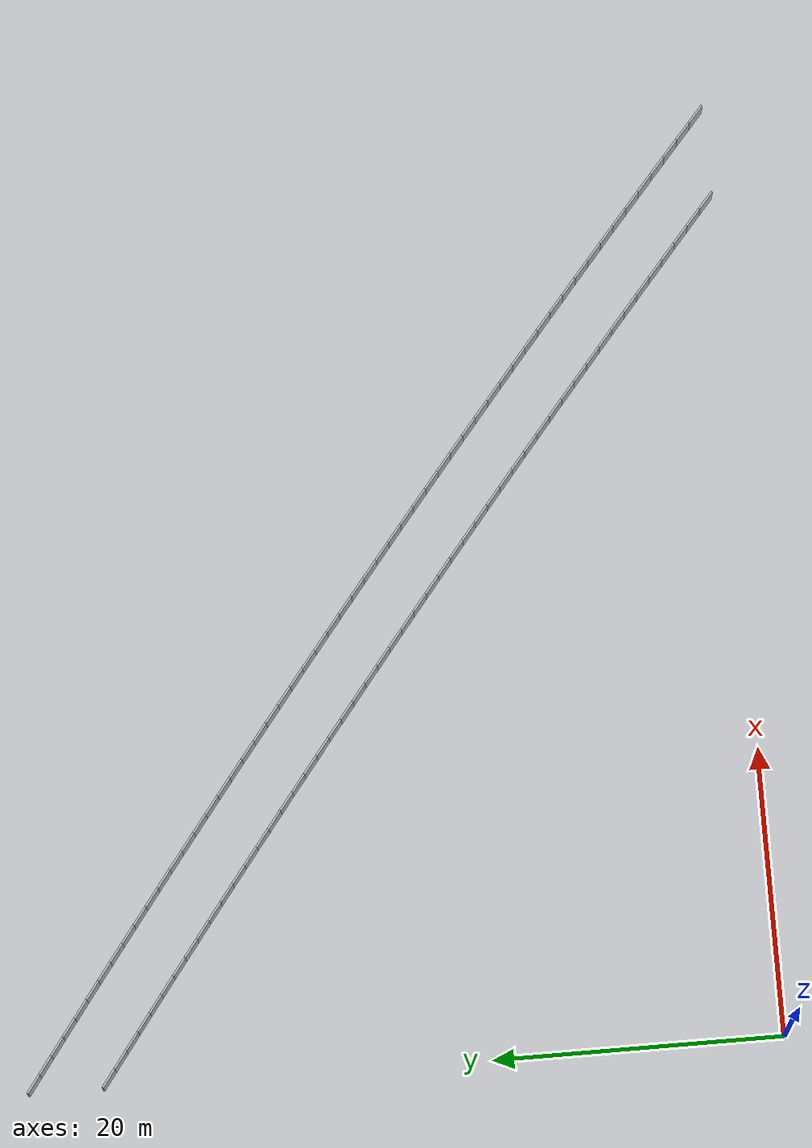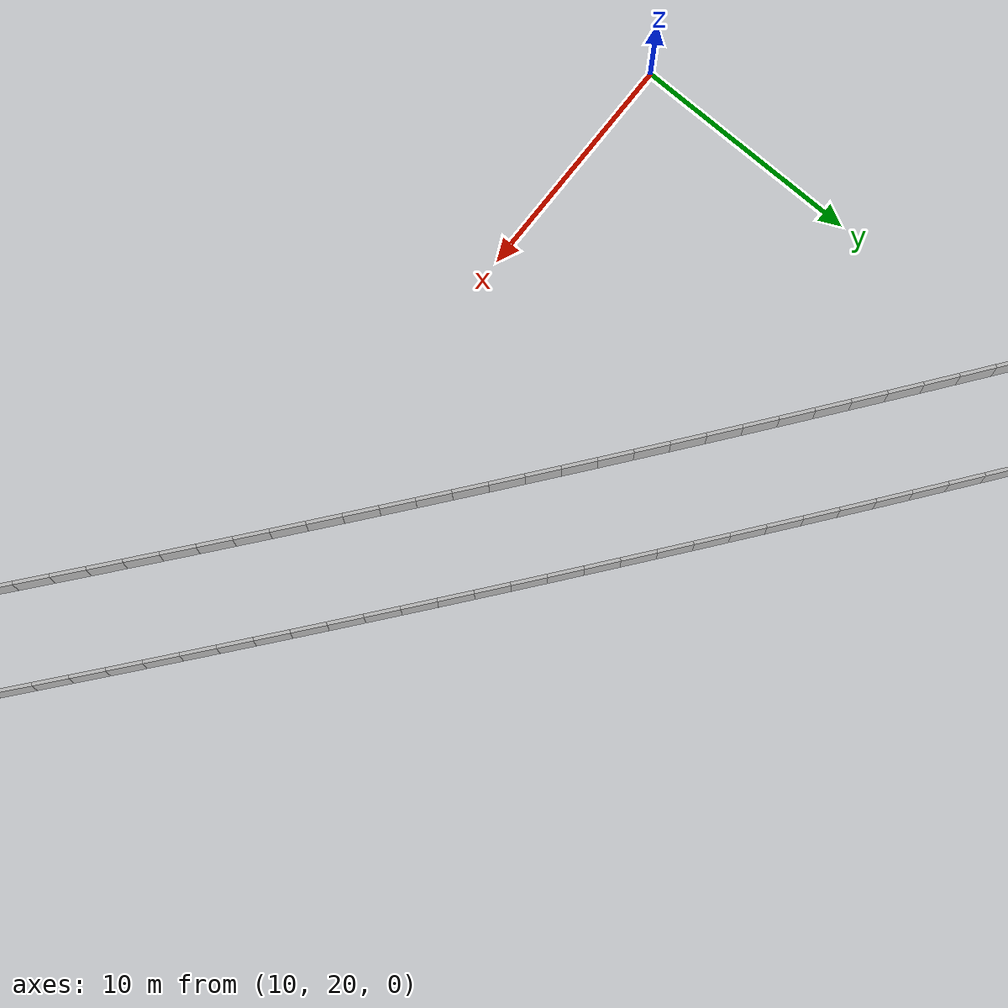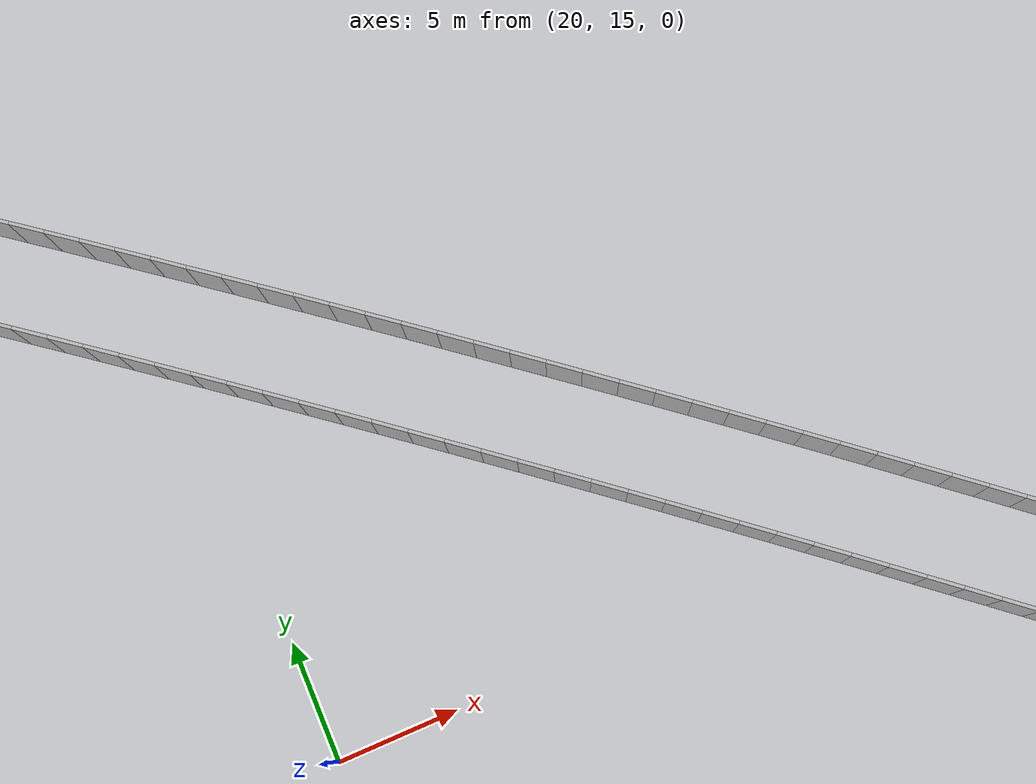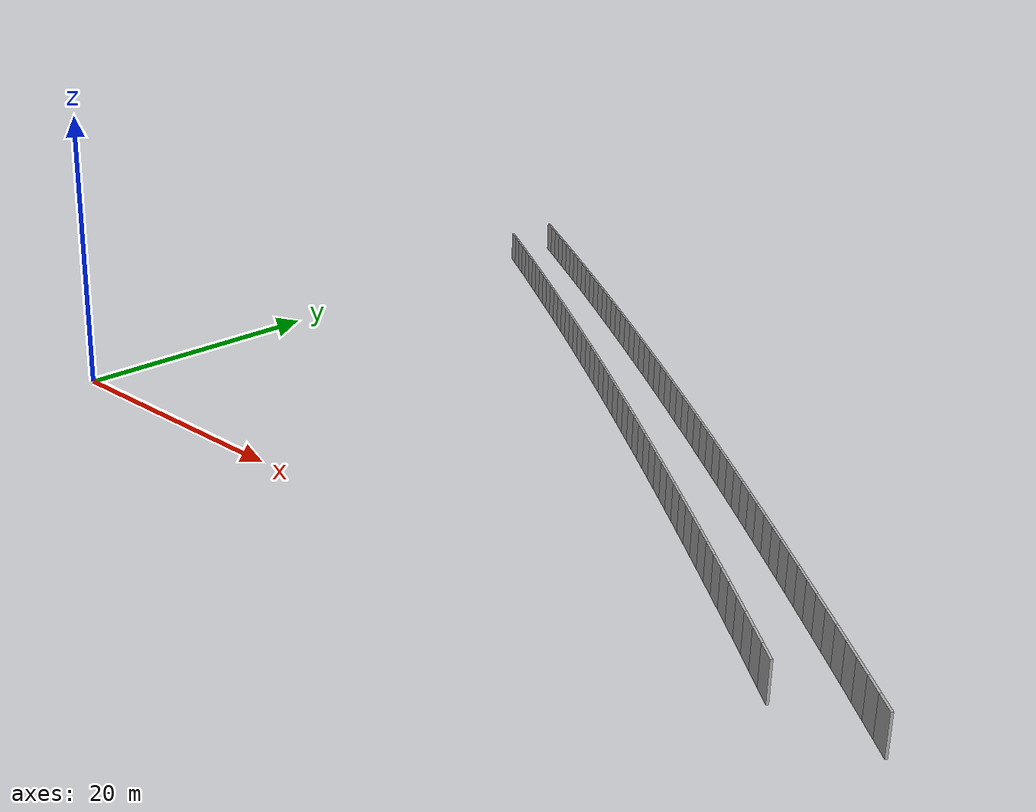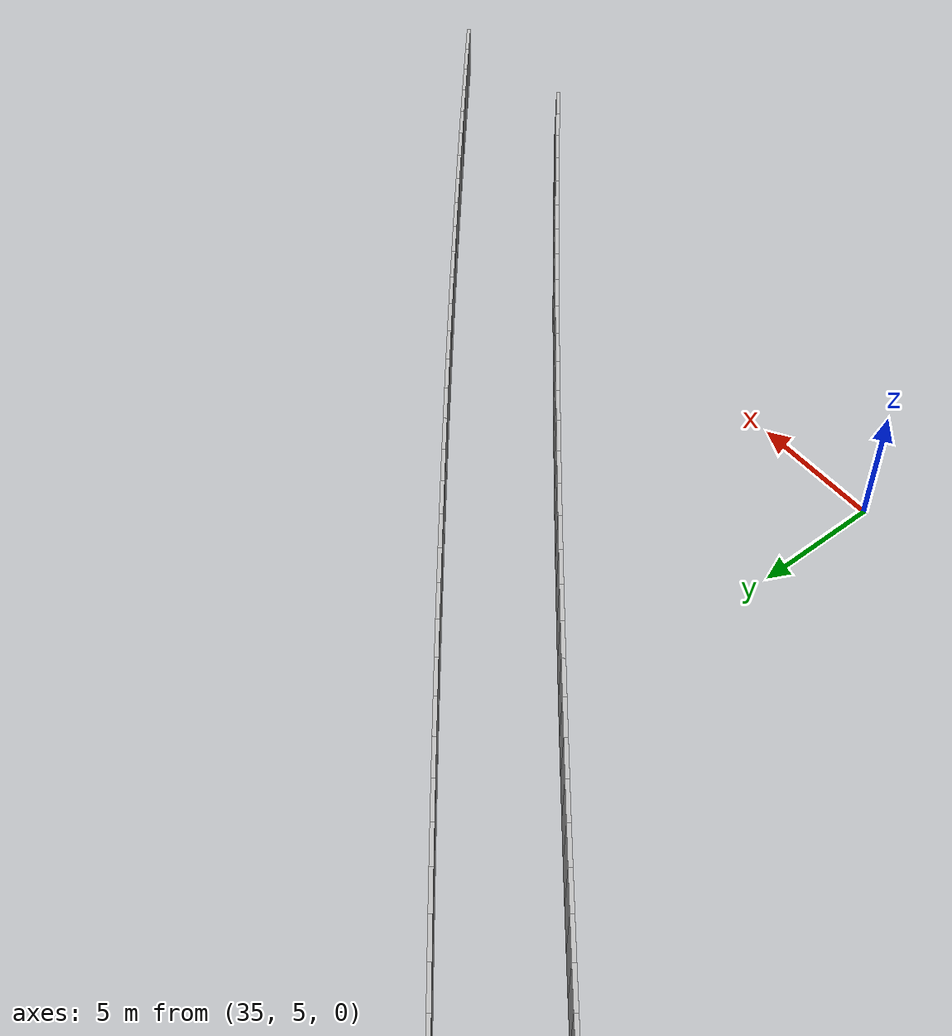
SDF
<?xml version="1.0" ?>
<sdf version="1.6">
  <model name="sps_1921">
    <pose frame="">0 0 0 0 -0 0</pose>
    <static>1</static>
    <self_collide>0</self_collide>
    <allow_auto_disable>0</allow_auto_disable>
    <link name="Wall10503">
      <kinematic>0</kinematic>
      <gravity>1</gravity>
      <self_collide>0</self_collide>
      <collision name="collision">
        <geometry>
          <box>
            <size>1.49645 0.15 2.5</size>
          </box>
        </geometry>
        <pose frame="">0 0 0 0 -0 0</pose>
      </collision>
      <visual name="visual">
        <geometry>
          <box>
            <size>1.49645 0.15 2.5</size>
          </box>
        </geometry>
        <pose frame="">0 0 0 0 -0 0</pose>
        <cast_shadows>1</cast_shadows>
        <transparency>0.0</transparency>
      </visual>
      <pose frame="">58.0063 0.326583 1.25 0 -0 2.42807</pose>
    </link>
    <link name="Wall10504">
      <kinematic>0</kinematic>
      <gravity>1</gravity>
      <self_collide>0</self_collide>
      <collision name="collision">
        <geometry>
          <box>
            <size>1.49658 0.15 2.5</size>
          </box>
        </geometry>
        <pose frame="">0 0 0 0 -0 0</pose>
      </collision>
      <visual name="visual">
        <geometry>
          <box>
            <size>1.49658 0.15 2.5</size>
          </box>
        </geometry>
        <pose frame="">0 0 0 0 -0 0</pose>
        <cast_shadows>1</cast_shadows>
        <transparency>0.0</transparency>
      </visual>
      <pose frame="">56.8741 1.30519 1.25 0 -0 2.4296</pose>
    </link>
    <link name="Wall10505">
      <kinematic>0</kinematic>
      <gravity>1</gravity>
      <self_collide>0</self_collide>
      <collision name="collision">
        <geometry>
          <box>
            <size>1.49636 0.15 2.5</size>
          </box>
        </geometry>
        <pose frame="">0 0 0 0 -0 0</pose>
      </collision>
      <visual name="visual">
        <geometry>
          <box>
            <size>1.49636 0.15 2.5</size>
          </box>
        </geometry>
        <pose frame="">0 0 0 0 -0 0</pose>
        <cast_shadows>1</cast_shadows>
        <transparency>0.0</transparency>
      </visual>
      <pose frame="">55.7404 2.282 1.25 0 -0 2.4312</pose>
    </link>
    <link name="Wall10506">
      <kinematic>0</kinematic>
      <gravity>1</gravity>
      <self_collide>0</self_collide>
      <collision name="collision">
        <geometry>
          <box>
            <size>1.49677 0.15 2.5</size>
          </box>
        </geometry>
        <pose frame="">0 0 0 0 -0 0</pose>
      </collision>
      <visual name="visual">
        <geometry>
          <box>
            <size>1.49677 0.15 2.5</size>
          </box>
        </geometry>
        <pose frame="">0 0 0 0 -0 0</pose>
        <cast_shadows>1</cast_shadows>
        <transparency>0.0</transparency>
      </visual>
      <pose frame="">54.6052 3.25722 1.25 0 -0 2.43251</pose>
    </link>
    <link name="Wall10507">
      <kinematic>0</kinematic>
      <gravity>1</gravity>
      <self_collide>0</self_collide>
      <collision name="collision">
        <geometry>
          <box>
            <size>1.49639 0.15 2.5</size>
          </box>
        </geometry>
        <pose frame="">0 0 0 0 -0 0</pose>
      </collision>
      <visual name="visual">
        <geometry>
          <box>
            <size>1.49639 0.15 2.5</size>
          </box>
        </geometry>
        <pose frame="">0 0 0 0 -0 0</pose>
        <cast_shadows>1</cast_shadows>
        <transparency>0.0</transparency>
      </visual>
      <pose frame="">53.4685 4.23061 1.25 0 -0 2.43444</pose>
    </link>
    <link name="Wall10508">
      <kinematic>0</kinematic>
      <gravity>1</gravity>
      <self_collide>0</self_collide>
      <collision name="collision">
        <geometry>
          <box>
            <size>1.49647 0.15 2.5</size>
          </box>
        </geometry>
        <pose frame="">0 0 0 0 -0 0</pose>
      </collision>
      <visual name="visual">
        <geometry>
          <box>
            <size>1.49647 0.15 2.5</size>
          </box>
        </geometry>
        <pose frame="">0 0 0 0 -0 0</pose>
        <cast_shadows>1</cast_shadows>
        <transparency>0.0</transparency>
      </visual>
      <pose frame="">52.3302 5.20198 1.25 0 -0 2.43588</pose>
    </link>
    <link name="Wall10509">
      <kinematic>0</kinematic>
      <gravity>1</gravity>
      <self_collide>0</self_collide>
      <collision name="collision">
        <geometry>
          <box>
            <size>1.49637 0.15 2.5</size>
          </box>
        </geometry>
        <pose frame="">0 0 0 0 -0 0</pose>
      </collision>
      <visual name="visual">
        <geometry>
          <box>
            <size>1.49637 0.15 2.5</size>
          </box>
        </geometry>
        <pose frame="">0 0 0 0 -0 0</pose>
        <cast_shadows>1</cast_shadows>
        <transparency>0.0</transparency>
      </visual>
      <pose frame="">51.1904 6.17158 1.25 0 -0 2.43753</pose>
    </link>
    <link name="Wall10510">
      <kinematic>0</kinematic>
      <gravity>1</gravity>
      <self_collide>0</self_collide>
      <collision name="collision">
        <geometry>
          <box>
            <size>1.49644 0.15 2.5</size>
          </box>
        </geometry>
        <pose frame="">0 0 0 0 -0 0</pose>
      </collision>
      <visual name="visual">
        <geometry>
          <box>
            <size>1.49644 0.15 2.5</size>
          </box>
        </geometry>
        <pose frame="">0 0 0 0 -0 0</pose>
        <cast_shadows>1</cast_shadows>
        <transparency>0.0</transparency>
      </visual>
      <pose frame="">50.049 7.1393 1.25 0 -0 2.43918</pose>
    </link>
    <link name="Wall10511">
      <kinematic>0</kinematic>
      <gravity>1</gravity>
      <self_collide>0</self_collide>
      <collision name="collision">
        <geometry>
          <box>
            <size>1.49663 0.15 2.5</size>
          </box>
        </geometry>
        <pose frame="">0 0 0 0 -0 0</pose>
      </collision>
      <visual name="visual">
        <geometry>
          <box>
            <size>1.49663 0.15 2.5</size>
          </box>
        </geometry>
        <pose frame="">0 0 0 0 -0 0</pose>
        <cast_shadows>1</cast_shadows>
        <transparency>0.0</transparency>
      </visual>
      <pose frame="">48.906 8.1053 1.25 0 -0 2.44067</pose>
    </link>
    <link name="Wall10512">
      <kinematic>0</kinematic>
      <gravity>1</gravity>
      <self_collide>0</self_collide>
      <collision name="collision">
        <geometry>
          <box>
            <size>1.49655 0.15 2.5</size>
          </box>
        </geometry>
        <pose frame="">0 0 0 0 -0 0</pose>
      </collision>
      <visual name="visual">
        <geometry>
          <box>
            <size>1.49655 0.15 2.5</size>
          </box>
        </geometry>
        <pose frame="">0 0 0 0 -0 0</pose>
        <cast_shadows>1</cast_shadows>
        <transparency>0.0</transparency>
      </visual>
      <pose frame="">47.7614 9.0695 1.25 0 -0 2.44238</pose>
    </link>
    <link name="Wall10513">
      <kinematic>0</kinematic>
      <gravity>1</gravity>
      <self_collide>0</self_collide>
      <collision name="collision">
        <geometry>
          <box>
            <size>1.49649 0.15 2.5</size>
          </box>
        </geometry>
        <pose frame="">0 0 0 0 -0 0</pose>
      </collision>
      <visual name="visual">
        <geometry>
          <box>
            <size>1.49649 0.15 2.5</size>
          </box>
        </geometry>
        <pose frame="">0 0 0 0 -0 0</pose>
        <cast_shadows>1</cast_shadows>
        <transparency>0.0</transparency>
      </visual>
      <pose frame="">46.6153 10.0318 1.25 0 -0 2.44395</pose>
    </link>
    <link name="Wall10514">
      <kinematic>0</kinematic>
      <gravity>1</gravity>
      <self_collide>0</self_collide>
      <collision name="collision">
        <geometry>
          <box>
            <size>1.49642 0.15 2.5</size>
          </box>
        </geometry>
        <pose frame="">0 0 0 0 -0 0</pose>
      </collision>
      <visual name="visual">
        <geometry>
          <box>
            <size>1.49642 0.15 2.5</size>
          </box>
        </geometry>
        <pose frame="">0 0 0 0 -0 0</pose>
        <cast_shadows>1</cast_shadows>
        <transparency>0.0</transparency>
      </visual>
      <pose frame="">45.4677 10.9923 1.25 0 -0 2.4454</pose>
    </link>
    <link name="Wall10515">
      <kinematic>0</kinematic>
      <gravity>1</gravity>
      <self_collide>0</self_collide>
      <collision name="collision">
        <geometry>
          <box>
            <size>1.49657 0.15 2.5</size>
          </box>
        </geometry>
        <pose frame="">0 0 0 0 -0 0</pose>
      </collision>
      <visual name="visual">
        <geometry>
          <box>
            <size>1.49657 0.15 2.5</size>
          </box>
        </geometry>
        <pose frame="">0 0 0 0 -0 0</pose>
        <cast_shadows>1</cast_shadows>
        <transparency>0.0</transparency>
      </visual>
      <pose frame="">44.3187 11.951 1.25 0 -0 2.44713</pose>
    </link>
    <link name="Wall10516">
      <kinematic>0</kinematic>
      <gravity>1</gravity>
      <self_collide>0</self_collide>
      <collision name="collision">
        <geometry>
          <box>
            <size>1.49657 0.15 2.5</size>
          </box>
        </geometry>
        <pose frame="">0 0 0 0 -0 0</pose>
      </collision>
      <visual name="visual">
        <geometry>
          <box>
            <size>1.49657 0.15 2.5</size>
          </box>
        </geometry>
        <pose frame="">0 0 0 0 -0 0</pose>
        <cast_shadows>1</cast_shadows>
        <transparency>0.0</transparency>
      </visual>
      <pose frame="">43.168 12.9079 1.25 0 -0 2.44867</pose>
    </link>
    <link name="Wall10517">
      <kinematic>0</kinematic>
      <gravity>1</gravity>
      <self_collide>0</self_collide>
      <collision name="collision">
        <geometry>
          <box>
            <size>1.49647 0.15 2.5</size>
          </box>
        </geometry>
        <pose frame="">0 0 0 0 -0 0</pose>
      </collision>
      <visual name="visual">
        <geometry>
          <box>
            <size>1.49647 0.15 2.5</size>
          </box>
        </geometry>
        <pose frame="">0 0 0 0 -0 0</pose>
        <cast_shadows>1</cast_shadows>
        <transparency>0.0</transparency>
      </visual>
      <pose frame="">42.0159 13.863 1.25 0 -0 2.45015</pose>
    </link>
    <link name="Wall10518">
      <kinematic>0</kinematic>
      <gravity>1</gravity>
      <self_collide>0</self_collide>
      <collision name="collision">
        <geometry>
          <box>
            <size>1.49657 0.15 2.5</size>
          </box>
        </geometry>
        <pose frame="">0 0 0 0 -0 0</pose>
      </collision>
      <visual name="visual">
        <geometry>
          <box>
            <size>1.49657 0.15 2.5</size>
          </box>
        </geometry>
        <pose frame="">0 0 0 0 -0 0</pose>
        <cast_shadows>1</cast_shadows>
        <transparency>0.0</transparency>
      </visual>
      <pose frame="">40.8623 14.8163 1.25 0 -0 2.45179</pose>
    </link>
    <link name="Wall10519">
      <kinematic>0</kinematic>
      <gravity>1</gravity>
      <self_collide>0</self_collide>
      <collision name="collision">
        <geometry>
          <box>
            <size>1.49653 0.15 2.5</size>
          </box>
        </geometry>
        <pose frame="">0 0 0 0 -0 0</pose>
      </collision>
      <visual name="visual">
        <geometry>
          <box>
            <size>1.49653 0.15 2.5</size>
          </box>
        </geometry>
        <pose frame="">0 0 0 0 -0 0</pose>
        <cast_shadows>1</cast_shadows>
        <transparency>0.0</transparency>
      </visual>
      <pose frame="">39.7071 15.7678 1.25 0 -0 2.4533</pose>
    </link>
    <link name="Wall10520">
      <kinematic>0</kinematic>
      <gravity>1</gravity>
      <self_collide>0</self_collide>
      <collision name="collision">
        <geometry>
          <box>
            <size>1.49655 0.15 2.5</size>
          </box>
        </geometry>
        <pose frame="">0 0 0 0 -0 0</pose>
      </collision>
      <visual name="visual">
        <geometry>
          <box>
            <size>1.49655 0.15 2.5</size>
          </box>
        </geometry>
        <pose frame="">0 0 0 0 -0 0</pose>
        <cast_shadows>1</cast_shadows>
        <transparency>0.0</transparency>
      </visual>
      <pose frame="">38.5506 16.7175 1.25 0 -0 2.4549</pose>
    </link>
    <link name="Wall10521">
      <kinematic>0</kinematic>
      <gravity>1</gravity>
      <self_collide>0</self_collide>
      <collision name="collision">
        <geometry>
          <box>
            <size>1.49641 0.15 2.5</size>
          </box>
        </geometry>
        <pose frame="">0 0 0 0 -0 0</pose>
      </collision>
      <visual name="visual">
        <geometry>
          <box>
            <size>1.49641 0.15 2.5</size>
          </box>
        </geometry>
        <pose frame="">0 0 0 0 -0 0</pose>
        <cast_shadows>1</cast_shadows>
        <transparency>0.0</transparency>
      </visual>
      <pose frame="">37.3925 17.6653 1.25 0 -0 2.45656</pose>
    </link>
    <link name="Wall10522">
      <kinematic>0</kinematic>
      <gravity>1</gravity>
      <self_collide>0</self_collide>
      <collision name="collision">
        <geometry>
          <box>
            <size>1.49652 0.15 2.5</size>
          </box>
        </geometry>
        <pose frame="">0 0 0 0 -0 0</pose>
      </collision>
      <visual name="visual">
        <geometry>
          <box>
            <size>1.49652 0.15 2.5</size>
          </box>
        </geometry>
        <pose frame="">0 0 0 0 -0 0</pose>
        <cast_shadows>1</cast_shadows>
        <transparency>0.0</transparency>
      </visual>
      <pose frame="">36.2329 18.6112 1.25 0 -0 2.45814</pose>
    </link>
    <link name="Wall10523">
      <kinematic>0</kinematic>
      <gravity>1</gravity>
      <self_collide>0</self_collide>
      <collision name="collision">
        <geometry>
          <box>
            <size>1.49659 0.15 2.5</size>
          </box>
        </geometry>
        <pose frame="">0 0 0 0 -0 0</pose>
      </collision>
      <visual name="visual">
        <geometry>
          <box>
            <size>1.49659 0.15 2.5</size>
          </box>
        </geometry>
        <pose frame="">0 0 0 0 -0 0</pose>
        <cast_shadows>1</cast_shadows>
        <transparency>0.0</transparency>
      </visual>
      <pose frame="">35.0717 19.5553 1.25 0 -0 2.45976</pose>
    </link>
    <link name="Wall10524">
      <kinematic>0</kinematic>
      <gravity>1</gravity>
      <self_collide>0</self_collide>
      <collision name="collision">
        <geometry>
          <box>
            <size>1.4965 0.15 2.5</size>
          </box>
        </geometry>
        <pose frame="">0 0 0 0 -0 0</pose>
      </collision>
      <visual name="visual">
        <geometry>
          <box>
            <size>1.4965 0.15 2.5</size>
          </box>
        </geometry>
        <pose frame="">0 0 0 0 -0 0</pose>
        <cast_shadows>1</cast_shadows>
        <transparency>0.0</transparency>
      </visual>
      <pose frame="">33.909 20.4975 1.25 0 -0 2.46139</pose>
    </link>
    <link name="Wall10525">
      <kinematic>0</kinematic>
      <gravity>1</gravity>
      <self_collide>0</self_collide>
      <collision name="collision">
        <geometry>
          <box>
            <size>1.49651 0.15 2.5</size>
          </box>
        </geometry>
        <pose frame="">0 0 0 0 -0 0</pose>
      </collision>
      <visual name="visual">
        <geometry>
          <box>
            <size>1.49651 0.15 2.5</size>
          </box>
        </geometry>
        <pose frame="">0 0 0 0 -0 0</pose>
        <cast_shadows>1</cast_shadows>
        <transparency>0.0</transparency>
      </visual>
      <pose frame="">32.7448 21.4379 1.25 0 -0 2.46281</pose>
    </link>
    <link name="Wall10526">
      <kinematic>0</kinematic>
      <gravity>1</gravity>
      <self_collide>0</self_collide>
      <collision name="collision">
        <geometry>
          <box>
            <size>1.49665 0.15 2.5</size>
          </box>
        </geometry>
        <pose frame="">0 0 0 0 -0 0</pose>
      </collision>
      <visual name="visual">
        <geometry>
          <box>
            <size>1.49665 0.15 2.5</size>
          </box>
        </geometry>
        <pose frame="">0 0 0 0 -0 0</pose>
        <cast_shadows>1</cast_shadows>
        <transparency>0.0</transparency>
      </visual>
      <pose frame="">31.5793 22.3767 1.25 0 -0 2.4642</pose>
    </link>
    <link name="Wall10527">
      <kinematic>0</kinematic>
      <gravity>1</gravity>
      <self_collide>0</self_collide>
      <collision name="collision">
        <geometry>
          <box>
            <size>1.49632 0.15 2.5</size>
          </box>
        </geometry>
        <pose frame="">0 0 0 0 -0 0</pose>
      </collision>
      <visual name="visual">
        <geometry>
          <box>
            <size>1.49632 0.15 2.5</size>
          </box>
        </geometry>
        <pose frame="">0 0 0 0 -0 0</pose>
        <cast_shadows>1</cast_shadows>
        <transparency>0.0</transparency>
      </visual>
      <pose frame="">30.4123 23.3135 1.25 0 -0 2.46616</pose>
    </link>
    <link name="Wall10528">
      <kinematic>0</kinematic>
      <gravity>1</gravity>
      <self_collide>0</self_collide>
      <collision name="collision">
        <geometry>
          <box>
            <size>1.49661 0.15 2.5</size>
          </box>
        </geometry>
        <pose frame="">0 0 0 0 -0 0</pose>
      </collision>
      <visual name="visual">
        <geometry>
          <box>
            <size>1.49661 0.15 2.5</size>
          </box>
        </geometry>
        <pose frame="">0 0 0 0 -0 0</pose>
        <cast_shadows>1</cast_shadows>
        <transparency>0.0</transparency>
      </visual>
      <pose frame="">29.2438 24.2483 1.25 0 -0 2.46762</pose>
    </link>
    <link name="Wall10529">
      <kinematic>0</kinematic>
      <gravity>1</gravity>
      <self_collide>0</self_collide>
      <collision name="collision">
        <geometry>
          <box>
            <size>1.49661 0.15 2.5</size>
          </box>
        </geometry>
        <pose frame="">0 0 0 0 -0 0</pose>
      </collision>
      <visual name="visual">
        <geometry>
          <box>
            <size>1.49661 0.15 2.5</size>
          </box>
        </geometry>
        <pose frame="">0 0 0 0 -0 0</pose>
        <cast_shadows>1</cast_shadows>
        <transparency>0.0</transparency>
      </visual>
      <pose frame="">28.0737 25.1814 1.25 0 -0 2.46919</pose>
    </link>
    <link name="Wall10530">
      <kinematic>0</kinematic>
      <gravity>1</gravity>
      <self_collide>0</self_collide>
      <collision name="collision">
        <geometry>
          <box>
            <size>1.4963 0.15 2.5</size>
          </box>
        </geometry>
        <pose frame="">0 0 0 0 -0 0</pose>
      </collision>
      <visual name="visual">
        <geometry>
          <box>
            <size>1.4963 0.15 2.5</size>
          </box>
        </geometry>
        <pose frame="">0 0 0 0 -0 0</pose>
        <cast_shadows>1</cast_shadows>
        <transparency>0.0</transparency>
      </visual>
      <pose frame="">26.9022 26.1126 1.25 0 -0 2.47069</pose>
    </link>
    <link name="Wall10531">
      <kinematic>0</kinematic>
      <gravity>1</gravity>
      <self_collide>0</self_collide>
      <collision name="collision">
        <geometry>
          <box>
            <size>1.49655 0.15 2.5</size>
          </box>
        </geometry>
        <pose frame="">0 0 0 0 -0 0</pose>
      </collision>
      <visual name="visual">
        <geometry>
          <box>
            <size>1.49655 0.15 2.5</size>
          </box>
        </geometry>
        <pose frame="">0 0 0 0 -0 0</pose>
        <cast_shadows>1</cast_shadows>
        <transparency>0.0</transparency>
      </visual>
      <pose frame="">25.7294 27.0419 1.25 0 -0 2.47239</pose>
    </link>
    <link name="Wall10532">
      <kinematic>0</kinematic>
      <gravity>1</gravity>
      <self_collide>0</self_collide>
      <collision name="collision">
        <geometry>
          <box>
            <size>1.4966 0.15 2.5</size>
          </box>
        </geometry>
        <pose frame="">0 0 0 0 -0 0</pose>
      </collision>
      <visual name="visual">
        <geometry>
          <box>
            <size>1.4966 0.15 2.5</size>
          </box>
        </geometry>
        <pose frame="">0 0 0 0 -0 0</pose>
        <cast_shadows>1</cast_shadows>
        <transparency>0.0</transparency>
      </visual>
      <pose frame="">24.5548 27.9693 1.25 0 -0 2.47413</pose>
    </link>
    <link name="Wall10533">
      <kinematic>0</kinematic>
      <gravity>1</gravity>
      <self_collide>0</self_collide>
      <collision name="collision">
        <geometry>
          <box>
            <size>1.49642 0.15 2.5</size>
          </box>
        </geometry>
        <pose frame="">0 0 0 0 -0 0</pose>
      </collision>
      <visual name="visual">
        <geometry>
          <box>
            <size>1.49642 0.15 2.5</size>
          </box>
        </geometry>
        <pose frame="">0 0 0 0 -0 0</pose>
        <cast_shadows>1</cast_shadows>
        <transparency>0.0</transparency>
      </visual>
      <pose frame="">23.3787 28.8948 1.25 0 -0 2.47559</pose>
    </link>
    <link name="Wall10534">
      <kinematic>0</kinematic>
      <gravity>1</gravity>
      <self_collide>0</self_collide>
      <collision name="collision">
        <geometry>
          <box>
            <size>1.49657 0.15 2.5</size>
          </box>
        </geometry>
        <pose frame="">0 0 0 0 -0 0</pose>
      </collision>
      <visual name="visual">
        <geometry>
          <box>
            <size>1.49657 0.15 2.5</size>
          </box>
        </geometry>
        <pose frame="">0 0 0 0 -0 0</pose>
        <cast_shadows>1</cast_shadows>
        <transparency>0.0</transparency>
      </visual>
      <pose frame="">22.2013 29.8185 1.25 0 -0 2.47712</pose>
    </link>
    <link name="Wall10535">
      <kinematic>0</kinematic>
      <gravity>1</gravity>
      <self_collide>0</self_collide>
      <collision name="collision">
        <geometry>
          <box>
            <size>1.49656 0.15 2.5</size>
          </box>
        </geometry>
        <pose frame="">0 0 0 0 -0 0</pose>
      </collision>
      <visual name="visual">
        <geometry>
          <box>
            <size>1.49656 0.15 2.5</size>
          </box>
        </geometry>
        <pose frame="">0 0 0 0 -0 0</pose>
        <cast_shadows>1</cast_shadows>
        <transparency>0.0</transparency>
      </visual>
      <pose frame="">21.0225 30.7404 1.25 0 -0 2.47872</pose>
    </link>
    <link name="Wall10536">
      <kinematic>0</kinematic>
      <gravity>1</gravity>
      <self_collide>0</self_collide>
      <collision name="collision">
        <geometry>
          <box>
            <size>1.49661 0.15 2.5</size>
          </box>
        </geometry>
        <pose frame="">0 0 0 0 -0 0</pose>
      </collision>
      <visual name="visual">
        <geometry>
          <box>
            <size>1.49661 0.15 2.5</size>
          </box>
        </geometry>
        <pose frame="">0 0 0 0 -0 0</pose>
        <cast_shadows>1</cast_shadows>
        <transparency>0.0</transparency>
      </visual>
      <pose frame="">19.842 31.6604 1.25 0 -0 2.4804</pose>
    </link>
    <link name="Wall10537">
      <kinematic>0</kinematic>
      <gravity>1</gravity>
      <self_collide>0</self_collide>
      <collision name="collision">
        <geometry>
          <box>
            <size>1.4964 0.15 2.5</size>
          </box>
        </geometry>
        <pose frame="">0 0 0 0 -0 0</pose>
      </collision>
      <visual name="visual">
        <geometry>
          <box>
            <size>1.4964 0.15 2.5</size>
          </box>
        </geometry>
        <pose frame="">0 0 0 0 -0 0</pose>
        <cast_shadows>1</cast_shadows>
        <transparency>0.0</transparency>
      </visual>
      <pose frame="">18.6602 32.5785 1.25 0 -0 2.48184</pose>
    </link>
    <link name="Wall10538">
      <kinematic>0</kinematic>
      <gravity>1</gravity>
      <self_collide>0</self_collide>
      <collision name="collision">
        <geometry>
          <box>
            <size>1.49651 0.15 2.5</size>
          </box>
        </geometry>
        <pose frame="">0 0 0 0 -0 0</pose>
      </collision>
      <visual name="visual">
        <geometry>
          <box>
            <size>1.49651 0.15 2.5</size>
          </box>
        </geometry>
        <pose frame="">0 0 0 0 -0 0</pose>
        <cast_shadows>1</cast_shadows>
        <transparency>0.0</transparency>
      </visual>
      <pose frame="">17.477 33.4947 1.25 0 -0 2.48355</pose>
    </link>
    <link name="Wall10539">
      <kinematic>0</kinematic>
      <gravity>1</gravity>
      <self_collide>0</self_collide>
      <collision name="collision">
        <geometry>
          <box>
            <size>1.49645 0.15 2.5</size>
          </box>
        </geometry>
        <pose frame="">0 0 0 0 -0 0</pose>
      </collision>
      <visual name="visual">
        <geometry>
          <box>
            <size>1.49645 0.15 2.5</size>
          </box>
        </geometry>
        <pose frame="">0 0 0 0 -0 0</pose>
        <cast_shadows>1</cast_shadows>
        <transparency>0.0</transparency>
      </visual>
      <pose frame="">16.2924 34.409 1.25 0 -0 2.48506</pose>
    </link>
    <link name="Wall10540">
      <kinematic>0</kinematic>
      <gravity>1</gravity>
      <self_collide>0</self_collide>
      <collision name="collision">
        <geometry>
          <box>
            <size>1.49653 0.15 2.5</size>
          </box>
        </geometry>
        <pose frame="">0 0 0 0 -0 0</pose>
      </collision>
      <visual name="visual">
        <geometry>
          <box>
            <size>1.49653 0.15 2.5</size>
          </box>
        </geometry>
        <pose frame="">0 0 0 0 -0 0</pose>
        <cast_shadows>1</cast_shadows>
        <transparency>0.0</transparency>
      </visual>
      <pose frame="">15.1063 35.3215 1.25 0 -0 2.4866</pose>
    </link>
    <link name="Wall10541">
      <kinematic>0</kinematic>
      <gravity>1</gravity>
      <self_collide>0</self_collide>
      <collision name="collision">
        <geometry>
          <box>
            <size>1.49663 0.15 2.5</size>
          </box>
        </geometry>
        <pose frame="">0 0 0 0 -0 0</pose>
      </collision>
      <visual name="visual">
        <geometry>
          <box>
            <size>1.49663 0.15 2.5</size>
          </box>
        </geometry>
        <pose frame="">0 0 0 0 -0 0</pose>
        <cast_shadows>1</cast_shadows>
        <transparency>0.0</transparency>
      </visual>
      <pose frame="">13.9187 36.2322 1.25 0 -0 2.48819</pose>
    </link>
    <link name="Wall10542">
      <kinematic>0</kinematic>
      <gravity>1</gravity>
      <self_collide>0</self_collide>
      <collision name="collision">
        <geometry>
          <box>
            <size>1.49646 0.15 2.5</size>
          </box>
        </geometry>
        <pose frame="">0 0 0 0 -0 0</pose>
      </collision>
      <visual name="visual">
        <geometry>
          <box>
            <size>1.49646 0.15 2.5</size>
          </box>
        </geometry>
        <pose frame="">0 0 0 0 -0 0</pose>
        <cast_shadows>1</cast_shadows>
        <transparency>0.0</transparency>
      </visual>
      <pose frame="">12.7296 37.1409 1.25 0 -0 2.48995</pose>
    </link>
    <link name="Wall10543">
      <kinematic>0</kinematic>
      <gravity>1</gravity>
      <self_collide>0</self_collide>
      <collision name="collision">
        <geometry>
          <box>
            <size>1.49662 0.15 2.5</size>
          </box>
        </geometry>
        <pose frame="">0 0 0 0 -0 0</pose>
      </collision>
      <visual name="visual">
        <geometry>
          <box>
            <size>1.49662 0.15 2.5</size>
          </box>
        </geometry>
        <pose frame="">0 0 0 0 -0 0</pose>
        <cast_shadows>1</cast_shadows>
        <transparency>0.0</transparency>
      </visual>
      <pose frame="">11.5391 38.0477 1.25 0 -0 2.49136</pose>
    </link>
    <link name="Wall10544">
      <kinematic>0</kinematic>
      <gravity>1</gravity>
      <self_collide>0</self_collide>
      <collision name="collision">
        <geometry>
          <box>
            <size>1.49636 0.15 2.5</size>
          </box>
        </geometry>
        <pose frame="">0 0 0 0 -0 0</pose>
      </collision>
      <visual name="visual">
        <geometry>
          <box>
            <size>1.49636 0.15 2.5</size>
          </box>
        </geometry>
        <pose frame="">0 0 0 0 -0 0</pose>
        <cast_shadows>1</cast_shadows>
        <transparency>0.0</transparency>
      </visual>
      <pose frame="">10.3472 38.9526 1.25 0 -0 2.49307</pose>
    </link>
    <link name="Wall10545">
      <kinematic>0</kinematic>
      <gravity>1</gravity>
      <self_collide>0</self_collide>
      <collision name="collision">
        <geometry>
          <box>
            <size>1.49664 0.15 2.5</size>
          </box>
        </geometry>
        <pose frame="">0 0 0 0 -0 0</pose>
      </collision>
      <visual name="visual">
        <geometry>
          <box>
            <size>1.49664 0.15 2.5</size>
          </box>
        </geometry>
        <pose frame="">0 0 0 0 -0 0</pose>
        <cast_shadows>1</cast_shadows>
        <transparency>0.0</transparency>
      </visual>
      <pose frame="">9.15395 39.8558 1.25 0 -0 2.49424</pose>
    </link>
    <link name="Wall10546">
      <kinematic>0</kinematic>
      <gravity>1</gravity>
      <self_collide>0</self_collide>
      <collision name="collision">
        <geometry>
          <box>
            <size>1.49643 0.15 2.5</size>
          </box>
        </geometry>
        <pose frame="">0 0 0 0 -0 0</pose>
      </collision>
      <visual name="visual">
        <geometry>
          <box>
            <size>1.49643 0.15 2.5</size>
          </box>
        </geometry>
        <pose frame="">0 0 0 0 -0 0</pose>
        <cast_shadows>1</cast_shadows>
        <transparency>0.0</transparency>
      </visual>
      <pose frame="">7.95934 40.7572 1.25 0 -0 2.49613</pose>
    </link>
    <link name="Wall10547">
      <kinematic>0</kinematic>
      <gravity>1</gravity>
      <self_collide>0</self_collide>
      <collision name="collision">
        <geometry>
          <box>
            <size>1.49664 0.15 2.5</size>
          </box>
        </geometry>
        <pose frame="">0 0 0 0 -0 0</pose>
      </collision>
      <visual name="visual">
        <geometry>
          <box>
            <size>1.49664 0.15 2.5</size>
          </box>
        </geometry>
        <pose frame="">0 0 0 0 -0 0</pose>
        <cast_shadows>1</cast_shadows>
        <transparency>0.0</transparency>
      </visual>
      <pose frame="">6.76314 41.6565 1.25 0 -0 2.49777</pose>
    </link>
    <link name="Wall10548">
      <kinematic>0</kinematic>
      <gravity>1</gravity>
      <self_collide>0</self_collide>
      <collision name="collision">
        <geometry>
          <box>
            <size>1.4964 0.15 2.5</size>
          </box>
        </geometry>
        <pose frame="">0 0 0 0 -0 0</pose>
      </collision>
      <visual name="visual">
        <geometry>
          <box>
            <size>1.4964 0.15 2.5</size>
          </box>
        </geometry>
        <pose frame="">0 0 0 0 -0 0</pose>
        <cast_shadows>1</cast_shadows>
        <transparency>0.0</transparency>
      </visual>
      <pose frame="">5.56554 42.5539 1.25 0 -0 2.49927</pose>
    </link>
    <link name="Wall10549">
      <kinematic>0</kinematic>
      <gravity>1</gravity>
      <self_collide>0</self_collide>
      <collision name="collision">
        <geometry>
          <box>
            <size>1.49647 0.15 2.5</size>
          </box>
        </geometry>
        <pose frame="">0 0 0 0 -0 0</pose>
      </collision>
      <visual name="visual">
        <geometry>
          <box>
            <size>1.49647 0.15 2.5</size>
          </box>
        </geometry>
        <pose frame="">0 0 0 0 -0 0</pose>
        <cast_shadows>1</cast_shadows>
        <transparency>0.0</transparency>
      </visual>
      <pose frame="">4.36657 43.4493 1.25 0 -0 2.50099</pose>
    </link>
    <link name="Wall10550">
      <kinematic>0</kinematic>
      <gravity>1</gravity>
      <self_collide>0</self_collide>
      <collision name="collision">
        <geometry>
          <box>
            <size>1.49655 0.15 2.5</size>
          </box>
        </geometry>
        <pose frame="">0 0 0 0 -0 0</pose>
      </collision>
      <visual name="visual">
        <geometry>
          <box>
            <size>1.49655 0.15 2.5</size>
          </box>
        </geometry>
        <pose frame="">0 0 0 0 -0 0</pose>
        <cast_shadows>1</cast_shadows>
        <transparency>0.0</transparency>
      </visual>
      <pose frame="">3.16607 44.3428 1.25 0 -0 2.50255</pose>
    </link>
    <link name="Wall10551">
      <kinematic>0</kinematic>
      <gravity>1</gravity>
      <self_collide>0</self_collide>
      <collision name="collision">
        <geometry>
          <box>
            <size>1.49657 0.15 2.5</size>
          </box>
        </geometry>
        <pose frame="">0 0 0 0 -0 0</pose>
      </collision>
      <visual name="visual">
        <geometry>
          <box>
            <size>1.49657 0.15 2.5</size>
          </box>
        </geometry>
        <pose frame="">0 0 0 0 -0 0</pose>
        <cast_shadows>1</cast_shadows>
        <transparency>0.0</transparency>
      </visual>
      <pose frame="">1.96416 45.2345 1.25 0 -0 2.50404</pose>
    </link>
    <link name="Wall10552">
      <kinematic>0</kinematic>
      <gravity>1</gravity>
      <self_collide>0</self_collide>
      <collision name="collision">
        <geometry>
          <box>
            <size>1.49655 0.15 2.5</size>
          </box>
        </geometry>
        <pose frame="">0 0 0 0 -0 0</pose>
      </collision>
      <visual name="visual">
        <geometry>
          <box>
            <size>1.49655 0.15 2.5</size>
          </box>
        </geometry>
        <pose frame="">0 0 0 0 -0 0</pose>
        <cast_shadows>1</cast_shadows>
        <transparency>0.0</transparency>
      </visual>
      <pose frame="">0.760856 46.1243 1.25 0 -0 2.5057</pose>
    </link>
    <link name="Wall11097">
      <kinematic>0</kinematic>
      <gravity>1</gravity>
      <self_collide>0</self_collide>
      <collision name="collision">
        <geometry>
          <box>
            <size>1.50326 0.15 2.5</size>
          </box>
        </geometry>
        <pose frame="">0 0 0 0 -0 0</pose>
      </collision>
      <visual name="visual">
        <geometry>
          <box>
            <size>1.50326 0.15 2.5</size>
          </box>
        </geometry>
        <pose frame="">0 0 0 0 -0 0</pose>
        <cast_shadows>1</cast_shadows>
        <transparency>0.0</transparency>
      </visual>
      <pose frame="">64.1182 0.49739 1.25 0 -0 2.42322</pose>
    </link>
    <link name="Wall11098">
      <kinematic>0</kinematic>
      <gravity>1</gravity>
      <self_collide>0</self_collide>
      <collision name="collision">
        <geometry>
          <box>
            <size>1.50296 0.15 2.5</size>
          </box>
        </geometry>
        <pose frame="">0 0 0 0 -0 0</pose>
      </collision>
      <visual name="visual">
        <geometry>
          <box>
            <size>1.50296 0.15 2.5</size>
          </box>
        </geometry>
        <pose frame="">0 0 0 0 -0 0</pose>
        <cast_shadows>1</cast_shadows>
        <transparency>0.0</transparency>
      </visual>
      <pose frame="">62.9856 1.4857 1.25 0 -0 2.42494</pose>
    </link>
    <link name="Wall11099">
      <kinematic>0</kinematic>
      <gravity>1</gravity>
      <self_collide>0</self_collide>
      <collision name="collision">
        <geometry>
          <box>
            <size>1.50303 0.15 2.5</size>
          </box>
        </geometry>
        <pose frame="">0 0 0 0 -0 0</pose>
      </collision>
      <visual name="visual">
        <geometry>
          <box>
            <size>1.50303 0.15 2.5</size>
          </box>
        </geometry>
        <pose frame="">0 0 0 0 -0 0</pose>
        <cast_shadows>1</cast_shadows>
        <transparency>0.0</transparency>
      </visual>
      <pose frame="">61.8516 2.47212 1.25 0 -0 2.42643</pose>
    </link>
    <link name="Wall11100">
      <kinematic>0</kinematic>
      <gravity>1</gravity>
      <self_collide>0</self_collide>
      <collision name="collision">
        <geometry>
          <box>
            <size>1.50307 0.15 2.5</size>
          </box>
        </geometry>
        <pose frame="">0 0 0 0 -0 0</pose>
      </collision>
      <visual name="visual">
        <geometry>
          <box>
            <size>1.50307 0.15 2.5</size>
          </box>
        </geometry>
        <pose frame="">0 0 0 0 -0 0</pose>
        <cast_shadows>1</cast_shadows>
        <transparency>0.0</transparency>
      </visual>
      <pose frame="">60.7161 3.4568 1.25 0 -0 2.42807</pose>
    </link>
    <link name="Wall11101">
      <kinematic>0</kinematic>
      <gravity>1</gravity>
      <self_collide>0</self_collide>
      <collision name="collision">
        <geometry>
          <box>
            <size>1.50312 0.15 2.5</size>
          </box>
        </geometry>
        <pose frame="">0 0 0 0 -0 0</pose>
      </collision>
      <visual name="visual">
        <geometry>
          <box>
            <size>1.50312 0.15 2.5</size>
          </box>
        </geometry>
        <pose frame="">0 0 0 0 -0 0</pose>
        <cast_shadows>1</cast_shadows>
        <transparency>0.0</transparency>
      </visual>
      <pose frame="">59.5788 4.43968 1.25 0 -0 2.42965</pose>
    </link>
    <link name="Wall11102">
      <kinematic>0</kinematic>
      <gravity>1</gravity>
      <self_collide>0</self_collide>
      <collision name="collision">
        <geometry>
          <box>
            <size>1.50302 0.15 2.5</size>
          </box>
        </geometry>
        <pose frame="">0 0 0 0 -0 0</pose>
      </collision>
      <visual name="visual">
        <geometry>
          <box>
            <size>1.50302 0.15 2.5</size>
          </box>
        </geometry>
        <pose frame="">0 0 0 0 -0 0</pose>
        <cast_shadows>1</cast_shadows>
        <transparency>0.0</transparency>
      </visual>
      <pose frame="">58.4401 5.42079 1.25 0 -0 2.43115</pose>
    </link>
    <link name="Wall11103">
      <kinematic>0</kinematic>
      <gravity>1</gravity>
      <self_collide>0</self_collide>
      <collision name="collision">
        <geometry>
          <box>
            <size>1.50329 0.15 2.5</size>
          </box>
        </geometry>
        <pose frame="">0 0 0 0 -0 0</pose>
      </collision>
      <visual name="visual">
        <geometry>
          <box>
            <size>1.50329 0.15 2.5</size>
          </box>
        </geometry>
        <pose frame="">0 0 0 0 -0 0</pose>
        <cast_shadows>1</cast_shadows>
        <transparency>0.0</transparency>
      </visual>
      <pose frame="">57.2999 6.40019 1.25 0 -0 2.43275</pose>
    </link>
    <link name="Wall11104">
      <kinematic>0</kinematic>
      <gravity>1</gravity>
      <self_collide>0</self_collide>
      <collision name="collision">
        <geometry>
          <box>
            <size>1.50302 0.15 2.5</size>
          </box>
        </geometry>
        <pose frame="">0 0 0 0 -0 0</pose>
      </collision>
      <visual name="visual">
        <geometry>
          <box>
            <size>1.50302 0.15 2.5</size>
          </box>
        </geometry>
        <pose frame="">0 0 0 0 -0 0</pose>
        <cast_shadows>1</cast_shadows>
        <transparency>0.0</transparency>
      </visual>
      <pose frame="">56.158 7.3777 1.25 0 -0 2.43446</pose>
    </link>
    <link name="Wall11105">
      <kinematic>0</kinematic>
      <gravity>1</gravity>
      <self_collide>0</self_collide>
      <collision name="collision">
        <geometry>
          <box>
            <size>1.50309 0.15 2.5</size>
          </box>
        </geometry>
        <pose frame="">0 0 0 0 -0 0</pose>
      </collision>
      <visual name="visual">
        <geometry>
          <box>
            <size>1.50309 0.15 2.5</size>
          </box>
        </geometry>
        <pose frame="">0 0 0 0 -0 0</pose>
        <cast_shadows>1</cast_shadows>
        <transparency>0.0</transparency>
      </visual>
      <pose frame="">55.0146 8.35341 1.25 0 -0 2.43579</pose>
    </link>
    <link name="Wall11106">
      <kinematic>0</kinematic>
      <gravity>1</gravity>
      <self_collide>0</self_collide>
      <collision name="collision">
        <geometry>
          <box>
            <size>1.50303 0.15 2.5</size>
          </box>
        </geometry>
        <pose frame="">0 0 0 0 -0 0</pose>
      </collision>
      <visual name="visual">
        <geometry>
          <box>
            <size>1.50303 0.15 2.5</size>
          </box>
        </geometry>
        <pose frame="">0 0 0 0 -0 0</pose>
        <cast_shadows>1</cast_shadows>
        <transparency>0.0</transparency>
      </visual>
      <pose frame="">53.8699 9.32741 1.25 0 -0 2.43746</pose>
    </link>
    <link name="Wall11107">
      <kinematic>0</kinematic>
      <gravity>1</gravity>
      <self_collide>0</self_collide>
      <collision name="collision">
        <geometry>
          <box>
            <size>1.50324 0.15 2.5</size>
          </box>
        </geometry>
        <pose frame="">0 0 0 0 -0 0</pose>
      </collision>
      <visual name="visual">
        <geometry>
          <box>
            <size>1.50324 0.15 2.5</size>
          </box>
        </geometry>
        <pose frame="">0 0 0 0 -0 0</pose>
        <cast_shadows>1</cast_shadows>
        <transparency>0.0</transparency>
      </visual>
      <pose frame="">52.7234 10.2995 1.25 0 -0 2.43918</pose>
    </link>
    <link name="Wall11108">
      <kinematic>0</kinematic>
      <gravity>1</gravity>
      <self_collide>0</self_collide>
      <collision name="collision">
        <geometry>
          <box>
            <size>1.50299 0.15 2.5</size>
          </box>
        </geometry>
        <pose frame="">0 0 0 0 -0 0</pose>
      </collision>
      <visual name="visual">
        <geometry>
          <box>
            <size>1.50299 0.15 2.5</size>
          </box>
        </geometry>
        <pose frame="">0 0 0 0 -0 0</pose>
        <cast_shadows>1</cast_shadows>
        <transparency>0.0</transparency>
      </visual>
      <pose frame="">51.5754 11.2698 1.25 0 -0 2.44063</pose>
    </link>
    <link name="Wall11109">
      <kinematic>0</kinematic>
      <gravity>1</gravity>
      <self_collide>0</self_collide>
      <collision name="collision">
        <geometry>
          <box>
            <size>1.50309 0.15 2.5</size>
          </box>
        </geometry>
        <pose frame="">0 0 0 0 -0 0</pose>
      </collision>
      <visual name="visual">
        <geometry>
          <box>
            <size>1.50309 0.15 2.5</size>
          </box>
        </geometry>
        <pose frame="">0 0 0 0 -0 0</pose>
        <cast_shadows>1</cast_shadows>
        <transparency>0.0</transparency>
      </visual>
      <pose frame="">50.4259 12.2382 1.25 0 -0 2.44238</pose>
    </link>
    <link name="Wall11110">
      <kinematic>0</kinematic>
      <gravity>1</gravity>
      <self_collide>0</self_collide>
      <collision name="collision">
        <geometry>
          <box>
            <size>1.50303 0.15 2.5</size>
          </box>
        </geometry>
        <pose frame="">0 0 0 0 -0 0</pose>
      </collision>
      <visual name="visual">
        <geometry>
          <box>
            <size>1.50303 0.15 2.5</size>
          </box>
        </geometry>
        <pose frame="">0 0 0 0 -0 0</pose>
        <cast_shadows>1</cast_shadows>
        <transparency>0.0</transparency>
      </visual>
      <pose frame="">49.2748 13.2047 1.25 0 -0 2.44389</pose>
    </link>
    <link name="Wall11111">
      <kinematic>0</kinematic>
      <gravity>1</gravity>
      <self_collide>0</self_collide>
      <collision name="collision">
        <geometry>
          <box>
            <size>1.50311 0.15 2.5</size>
          </box>
        </geometry>
        <pose frame="">0 0 0 0 -0 0</pose>
      </collision>
      <visual name="visual">
        <geometry>
          <box>
            <size>1.50311 0.15 2.5</size>
          </box>
        </geometry>
        <pose frame="">0 0 0 0 -0 0</pose>
        <cast_shadows>1</cast_shadows>
        <transparency>0.0</transparency>
      </visual>
      <pose frame="">48.1222 14.1694 1.25 0 -0 2.44552</pose>
    </link>
    <link name="Wall11112">
      <kinematic>0</kinematic>
      <gravity>1</gravity>
      <self_collide>0</self_collide>
      <collision name="collision">
        <geometry>
          <box>
            <size>1.50297 0.15 2.5</size>
          </box>
        </geometry>
        <pose frame="">0 0 0 0 -0 0</pose>
      </collision>
      <visual name="visual">
        <geometry>
          <box>
            <size>1.50297 0.15 2.5</size>
          </box>
        </geometry>
        <pose frame="">0 0 0 0 -0 0</pose>
        <cast_shadows>1</cast_shadows>
        <transparency>0.0</transparency>
      </visual>
      <pose frame="">46.968 15.1323 1.25 0 -0 2.44703</pose>
    </link>
    <link name="Wall11113">
      <kinematic>0</kinematic>
      <gravity>1</gravity>
      <self_collide>0</self_collide>
      <collision name="collision">
        <geometry>
          <box>
            <size>1.50318 0.15 2.5</size>
          </box>
        </geometry>
        <pose frame="">0 0 0 0 -0 0</pose>
      </collision>
      <visual name="visual">
        <geometry>
          <box>
            <size>1.50318 0.15 2.5</size>
          </box>
        </geometry>
        <pose frame="">0 0 0 0 -0 0</pose>
        <cast_shadows>1</cast_shadows>
        <transparency>0.0</transparency>
      </visual>
      <pose frame="">45.8125 16.0935 1.25 0 -0 2.44852</pose>
    </link>
    <link name="Wall11114">
      <kinematic>0</kinematic>
      <gravity>1</gravity>
      <self_collide>0</self_collide>
      <collision name="collision">
        <geometry>
          <box>
            <size>1.5029 0.15 2.5</size>
          </box>
        </geometry>
        <pose frame="">0 0 0 0 -0 0</pose>
      </collision>
      <visual name="visual">
        <geometry>
          <box>
            <size>1.5029 0.15 2.5</size>
          </box>
        </geometry>
        <pose frame="">0 0 0 0 -0 0</pose>
        <cast_shadows>1</cast_shadows>
        <transparency>0.0</transparency>
      </visual>
      <pose frame="">44.6554 17.0528 1.25 0 -0 2.45027</pose>
    </link>
    <link name="Wall11115">
      <kinematic>0</kinematic>
      <gravity>1</gravity>
      <self_collide>0</self_collide>
      <collision name="collision">
        <geometry>
          <box>
            <size>1.50326 0.15 2.5</size>
          </box>
        </geometry>
        <pose frame="">0 0 0 0 -0 0</pose>
      </collision>
      <visual name="visual">
        <geometry>
          <box>
            <size>1.50326 0.15 2.5</size>
          </box>
        </geometry>
        <pose frame="">0 0 0 0 -0 0</pose>
        <cast_shadows>1</cast_shadows>
        <transparency>0.0</transparency>
      </visual>
      <pose frame="">43.4966 18.0102 1.25 0 -0 2.45183</pose>
    </link>
    <link name="Wall11116">
      <kinematic>0</kinematic>
      <gravity>1</gravity>
      <self_collide>0</self_collide>
      <collision name="collision">
        <geometry>
          <box>
            <size>1.50317 0.15 2.5</size>
          </box>
        </geometry>
        <pose frame="">0 0 0 0 -0 0</pose>
      </collision>
      <visual name="visual">
        <geometry>
          <box>
            <size>1.50317 0.15 2.5</size>
          </box>
        </geometry>
        <pose frame="">0 0 0 0 -0 0</pose>
        <cast_shadows>1</cast_shadows>
        <transparency>0.0</transparency>
      </visual>
      <pose frame="">42.3364 18.9659 1.25 0 -0 2.45331</pose>
    </link>
    <link name="Wall11117">
      <kinematic>0</kinematic>
      <gravity>1</gravity>
      <self_collide>0</self_collide>
      <collision name="collision">
        <geometry>
          <box>
            <size>1.50298 0.15 2.5</size>
          </box>
        </geometry>
        <pose frame="">0 0 0 0 -0 0</pose>
      </collision>
      <visual name="visual">
        <geometry>
          <box>
            <size>1.50298 0.15 2.5</size>
          </box>
        </geometry>
        <pose frame="">0 0 0 0 -0 0</pose>
        <cast_shadows>1</cast_shadows>
        <transparency>0.0</transparency>
      </visual>
      <pose frame="">41.1747 19.9197 1.25 0 -0 2.45499</pose>
    </link>
    <link name="Wall11118">
      <kinematic>0</kinematic>
      <gravity>1</gravity>
      <self_collide>0</self_collide>
      <collision name="collision">
        <geometry>
          <box>
            <size>1.50313 0.15 2.5</size>
          </box>
        </geometry>
        <pose frame="">0 0 0 0 -0 0</pose>
      </collision>
      <visual name="visual">
        <geometry>
          <box>
            <size>1.50313 0.15 2.5</size>
          </box>
        </geometry>
        <pose frame="">0 0 0 0 -0 0</pose>
        <cast_shadows>1</cast_shadows>
        <transparency>0.0</transparency>
      </visual>
      <pose frame="">40.0115 20.8716 1.25 0 -0 2.45654</pose>
    </link>
    <link name="Wall11119">
      <kinematic>0</kinematic>
      <gravity>1</gravity>
      <self_collide>0</self_collide>
      <collision name="collision">
        <geometry>
          <box>
            <size>1.50302 0.15 2.5</size>
          </box>
        </geometry>
        <pose frame="">0 0 0 0 -0 0</pose>
      </collision>
      <visual name="visual">
        <geometry>
          <box>
            <size>1.50302 0.15 2.5</size>
          </box>
        </geometry>
        <pose frame="">0 0 0 0 -0 0</pose>
        <cast_shadows>1</cast_shadows>
        <transparency>0.0</transparency>
      </visual>
      <pose frame="">38.8468 21.8217 1.25 0 -0 2.45811</pose>
    </link>
    <link name="Wall11120">
      <kinematic>0</kinematic>
      <gravity>1</gravity>
      <self_collide>0</self_collide>
      <collision name="collision">
        <geometry>
          <box>
            <size>1.50302 0.15 2.5</size>
          </box>
        </geometry>
        <pose frame="">0 0 0 0 -0 0</pose>
      </collision>
      <visual name="visual">
        <geometry>
          <box>
            <size>1.50302 0.15 2.5</size>
          </box>
        </geometry>
        <pose frame="">0 0 0 0 -0 0</pose>
        <cast_shadows>1</cast_shadows>
        <transparency>0.0</transparency>
      </visual>
      <pose frame="">37.6806 22.7699 1.25 0 -0 2.45978</pose>
    </link>
    <link name="Wall11121">
      <kinematic>0</kinematic>
      <gravity>1</gravity>
      <self_collide>0</self_collide>
      <collision name="collision">
        <geometry>
          <box>
            <size>1.503 0.15 2.5</size>
          </box>
        </geometry>
        <pose frame="">0 0 0 0 -0 0</pose>
      </collision>
      <visual name="visual">
        <geometry>
          <box>
            <size>1.503 0.15 2.5</size>
          </box>
        </geometry>
        <pose frame="">0 0 0 0 -0 0</pose>
        <cast_shadows>1</cast_shadows>
        <transparency>0.0</transparency>
      </visual>
      <pose frame="">36.5129 23.7162 1.25 0 -0 2.46128</pose>
    </link>
    <link name="Wall11122">
      <kinematic>0</kinematic>
      <gravity>1</gravity>
      <self_collide>0</self_collide>
      <collision name="collision">
        <geometry>
          <box>
            <size>1.50313 0.15 2.5</size>
          </box>
        </geometry>
        <pose frame="">0 0 0 0 -0 0</pose>
      </collision>
      <visual name="visual">
        <geometry>
          <box>
            <size>1.50313 0.15 2.5</size>
          </box>
        </geometry>
        <pose frame="">0 0 0 0 -0 0</pose>
        <cast_shadows>1</cast_shadows>
        <transparency>0.0</transparency>
      </visual>
      <pose frame="">35.3437 24.6607 1.25 0 -0 2.46292</pose>
    </link>
    <link name="Wall11123">
      <kinematic>0</kinematic>
      <gravity>1</gravity>
      <self_collide>0</self_collide>
      <collision name="collision">
        <geometry>
          <box>
            <size>1.50302 0.15 2.5</size>
          </box>
        </geometry>
        <pose frame="">0 0 0 0 -0 0</pose>
      </collision>
      <visual name="visual">
        <geometry>
          <box>
            <size>1.50302 0.15 2.5</size>
          </box>
        </geometry>
        <pose frame="">0 0 0 0 -0 0</pose>
        <cast_shadows>1</cast_shadows>
        <transparency>0.0</transparency>
      </visual>
      <pose frame="">34.1729 25.6034 1.25 0 -0 2.46443</pose>
    </link>
    <link name="Wall11124">
      <kinematic>0</kinematic>
      <gravity>1</gravity>
      <self_collide>0</self_collide>
      <collision name="collision">
        <geometry>
          <box>
            <size>1.50304 0.15 2.5</size>
          </box>
        </geometry>
        <pose frame="">0 0 0 0 -0 0</pose>
      </collision>
      <visual name="visual">
        <geometry>
          <box>
            <size>1.50304 0.15 2.5</size>
          </box>
        </geometry>
        <pose frame="">0 0 0 0 -0 0</pose>
        <cast_shadows>1</cast_shadows>
        <transparency>0.0</transparency>
      </visual>
      <pose frame="">33.0008 26.5442 1.25 0 -0 2.4661</pose>
    </link>
    <link name="Wall11125">
      <kinematic>0</kinematic>
      <gravity>1</gravity>
      <self_collide>0</self_collide>
      <collision name="collision">
        <geometry>
          <box>
            <size>1.50308 0.15 2.5</size>
          </box>
        </geometry>
        <pose frame="">0 0 0 0 -0 0</pose>
      </collision>
      <visual name="visual">
        <geometry>
          <box>
            <size>1.50308 0.15 2.5</size>
          </box>
        </geometry>
        <pose frame="">0 0 0 0 -0 0</pose>
        <cast_shadows>1</cast_shadows>
        <transparency>0.0</transparency>
      </visual>
      <pose frame="">31.8272 27.4833 1.25 0 -0 2.46737</pose>
    </link>
    <link name="Wall11126">
      <kinematic>0</kinematic>
      <gravity>1</gravity>
      <self_collide>0</self_collide>
      <collision name="collision">
        <geometry>
          <box>
            <size>1.50318 0.15 2.5</size>
          </box>
        </geometry>
        <pose frame="">0 0 0 0 -0 0</pose>
      </collision>
      <visual name="visual">
        <geometry>
          <box>
            <size>1.50318 0.15 2.5</size>
          </box>
        </geometry>
        <pose frame="">0 0 0 0 -0 0</pose>
        <cast_shadows>1</cast_shadows>
        <transparency>0.0</transparency>
      </visual>
      <pose frame="">30.6521 28.4206 1.25 0 -0 2.46924</pose>
    </link>
    <link name="Wall11127">
      <kinematic>0</kinematic>
      <gravity>1</gravity>
      <self_collide>0</self_collide>
      <collision name="collision">
        <geometry>
          <box>
            <size>1.50309 0.15 2.5</size>
          </box>
        </geometry>
        <pose frame="">0 0 0 0 -0 0</pose>
      </collision>
      <visual name="visual">
        <geometry>
          <box>
            <size>1.50309 0.15 2.5</size>
          </box>
        </geometry>
        <pose frame="">0 0 0 0 -0 0</pose>
        <cast_shadows>1</cast_shadows>
        <transparency>0.0</transparency>
      </visual>
      <pose frame="">29.4754 29.3559 1.25 0 -0 2.47075</pose>
    </link>
    <link name="Wall11128">
      <kinematic>0</kinematic>
      <gravity>1</gravity>
      <self_collide>0</self_collide>
      <collision name="collision">
        <geometry>
          <box>
            <size>1.50302 0.15 2.5</size>
          </box>
        </geometry>
        <pose frame="">0 0 0 0 -0 0</pose>
      </collision>
      <visual name="visual">
        <geometry>
          <box>
            <size>1.50302 0.15 2.5</size>
          </box>
        </geometry>
        <pose frame="">0 0 0 0 -0 0</pose>
        <cast_shadows>1</cast_shadows>
        <transparency>0.0</transparency>
      </visual>
      <pose frame="">28.2972 30.2892 1.25 0 -0 2.47258</pose>
    </link>
    <link name="Wall11129">
      <kinematic>0</kinematic>
      <gravity>1</gravity>
      <self_collide>0</self_collide>
      <collision name="collision">
        <geometry>
          <box>
            <size>1.50313 0.15 2.5</size>
          </box>
        </geometry>
        <pose frame="">0 0 0 0 -0 0</pose>
      </collision>
      <visual name="visual">
        <geometry>
          <box>
            <size>1.50313 0.15 2.5</size>
          </box>
        </geometry>
        <pose frame="">0 0 0 0 -0 0</pose>
        <cast_shadows>1</cast_shadows>
        <transparency>0.0</transparency>
      </visual>
      <pose frame="">27.1175 31.2206 1.25 0 -0 2.47399</pose>
    </link>
    <link name="Wall11130">
      <kinematic>0</kinematic>
      <gravity>1</gravity>
      <self_collide>0</self_collide>
      <collision name="collision">
        <geometry>
          <box>
            <size>1.50309 0.15 2.5</size>
          </box>
        </geometry>
        <pose frame="">0 0 0 0 -0 0</pose>
      </collision>
      <visual name="visual">
        <geometry>
          <box>
            <size>1.50309 0.15 2.5</size>
          </box>
        </geometry>
        <pose frame="">0 0 0 0 -0 0</pose>
        <cast_shadows>1</cast_shadows>
        <transparency>0.0</transparency>
      </visual>
      <pose frame="">25.9364 32.1503 1.25 0 -0 2.47546</pose>
    </link>
    <link name="Wall11131">
      <kinematic>0</kinematic>
      <gravity>1</gravity>
      <self_collide>0</self_collide>
      <collision name="collision">
        <geometry>
          <box>
            <size>1.503 0.15 2.5</size>
          </box>
        </geometry>
        <pose frame="">0 0 0 0 -0 0</pose>
      </collision>
      <visual name="visual">
        <geometry>
          <box>
            <size>1.503 0.15 2.5</size>
          </box>
        </geometry>
        <pose frame="">0 0 0 0 -0 0</pose>
        <cast_shadows>1</cast_shadows>
        <transparency>0.0</transparency>
      </visual>
      <pose frame="">24.7539 33.0781 1.25 0 -0 2.47712</pose>
    </link>
    <link name="Wall11132">
      <kinematic>0</kinematic>
      <gravity>1</gravity>
      <self_collide>0</self_collide>
      <collision name="collision">
        <geometry>
          <box>
            <size>1.50313 0.15 2.5</size>
          </box>
        </geometry>
        <pose frame="">0 0 0 0 -0 0</pose>
      </collision>
      <visual name="visual">
        <geometry>
          <box>
            <size>1.50313 0.15 2.5</size>
          </box>
        </geometry>
        <pose frame="">0 0 0 0 -0 0</pose>
        <cast_shadows>1</cast_shadows>
        <transparency>0.0</transparency>
      </visual>
      <pose frame="">23.5698 34.004 1.25 0 -0 2.47873</pose>
    </link>
    <link name="Wall11133">
      <kinematic>0</kinematic>
      <gravity>1</gravity>
      <self_collide>0</self_collide>
      <collision name="collision">
        <geometry>
          <box>
            <size>1.50295 0.15 2.5</size>
          </box>
        </geometry>
        <pose frame="">0 0 0 0 -0 0</pose>
      </collision>
      <visual name="visual">
        <geometry>
          <box>
            <size>1.50295 0.15 2.5</size>
          </box>
        </geometry>
        <pose frame="">0 0 0 0 -0 0</pose>
        <cast_shadows>1</cast_shadows>
        <transparency>0.0</transparency>
      </visual>
      <pose frame="">22.3844 34.928 1.25 0 -0 2.48034</pose>
    </link>
    <link name="Wall11134">
      <kinematic>0</kinematic>
      <gravity>1</gravity>
      <self_collide>0</self_collide>
      <collision name="collision">
        <geometry>
          <box>
            <size>1.50302 0.15 2.5</size>
          </box>
        </geometry>
        <pose frame="">0 0 0 0 -0 0</pose>
      </collision>
      <visual name="visual">
        <geometry>
          <box>
            <size>1.50302 0.15 2.5</size>
          </box>
        </geometry>
        <pose frame="">0 0 0 0 -0 0</pose>
        <cast_shadows>1</cast_shadows>
        <transparency>0.0</transparency>
      </visual>
      <pose frame="">21.1975 35.8501 1.25 0 -0 2.48186</pose>
    </link>
    <link name="Wall11135">
      <kinematic>0</kinematic>
      <gravity>1</gravity>
      <self_collide>0</self_collide>
      <collision name="collision">
        <geometry>
          <box>
            <size>1.50319 0.15 2.5</size>
          </box>
        </geometry>
        <pose frame="">0 0 0 0 -0 0</pose>
      </collision>
      <visual name="visual">
        <geometry>
          <box>
            <size>1.50319 0.15 2.5</size>
          </box>
        </geometry>
        <pose frame="">0 0 0 0 -0 0</pose>
        <cast_shadows>1</cast_shadows>
        <transparency>0.0</transparency>
      </visual>
      <pose frame="">20.0091 36.7704 1.25 0 -0 2.48344</pose>
    </link>
    <link name="Wall11136">
      <kinematic>0</kinematic>
      <gravity>1</gravity>
      <self_collide>0</self_collide>
      <collision name="collision">
        <geometry>
          <box>
            <size>1.50303 0.15 2.5</size>
          </box>
        </geometry>
        <pose frame="">0 0 0 0 -0 0</pose>
      </collision>
      <visual name="visual">
        <geometry>
          <box>
            <size>1.50303 0.15 2.5</size>
          </box>
        </geometry>
        <pose frame="">0 0 0 0 -0 0</pose>
        <cast_shadows>1</cast_shadows>
        <transparency>0.0</transparency>
      </visual>
      <pose frame="">18.8191 37.6888 1.25 0 -0 2.4851</pose>
    </link>
    <link name="Wall11137">
      <kinematic>0</kinematic>
      <gravity>1</gravity>
      <self_collide>0</self_collide>
      <collision name="collision">
        <geometry>
          <box>
            <size>1.5031 0.15 2.5</size>
          </box>
        </geometry>
        <pose frame="">0 0 0 0 -0 0</pose>
      </collision>
      <visual name="visual">
        <geometry>
          <box>
            <size>1.5031 0.15 2.5</size>
          </box>
        </geometry>
        <pose frame="">0 0 0 0 -0 0</pose>
        <cast_shadows>1</cast_shadows>
        <transparency>0.0</transparency>
      </visual>
      <pose frame="">17.6277 38.6052 1.25 0 -0 2.48678</pose>
    </link>
    <link name="Wall11138">
      <kinematic>0</kinematic>
      <gravity>1</gravity>
      <self_collide>0</self_collide>
      <collision name="collision">
        <geometry>
          <box>
            <size>1.50294 0.15 2.5</size>
          </box>
        </geometry>
        <pose frame="">0 0 0 0 -0 0</pose>
      </collision>
      <visual name="visual">
        <geometry>
          <box>
            <size>1.50294 0.15 2.5</size>
          </box>
        </geometry>
        <pose frame="">0 0 0 0 -0 0</pose>
        <cast_shadows>1</cast_shadows>
        <transparency>0.0</transparency>
      </visual>
      <pose frame="">16.435 39.5197 1.25 0 -0 2.48818</pose>
    </link>
    <link name="Wall11139">
      <kinematic>0</kinematic>
      <gravity>1</gravity>
      <self_collide>0</self_collide>
      <collision name="collision">
        <geometry>
          <box>
            <size>1.50314 0.15 2.5</size>
          </box>
        </geometry>
        <pose frame="">0 0 0 0 -0 0</pose>
      </collision>
      <visual name="visual">
        <geometry>
          <box>
            <size>1.50314 0.15 2.5</size>
          </box>
        </geometry>
        <pose frame="">0 0 0 0 -0 0</pose>
        <cast_shadows>1</cast_shadows>
        <transparency>0.0</transparency>
      </visual>
      <pose frame="">15.2408 40.4324 1.25 0 -0 2.48982</pose>
    </link>
    <link name="Wall11140">
      <kinematic>0</kinematic>
      <gravity>1</gravity>
      <self_collide>0</self_collide>
      <collision name="collision">
        <geometry>
          <box>
            <size>1.50315 0.15 2.5</size>
          </box>
        </geometry>
        <pose frame="">0 0 0 0 -0 0</pose>
      </collision>
      <visual name="visual">
        <geometry>
          <box>
            <size>1.50315 0.15 2.5</size>
          </box>
        </geometry>
        <pose frame="">0 0 0 0 -0 0</pose>
        <cast_shadows>1</cast_shadows>
        <transparency>0.0</transparency>
      </visual>
      <pose frame="">14.0451 41.3433 1.25 0 -0 2.49135</pose>
    </link>
    <link name="Wall11141">
      <kinematic>0</kinematic>
      <gravity>1</gravity>
      <self_collide>0</self_collide>
      <collision name="collision">
        <geometry>
          <box>
            <size>1.50308 0.15 2.5</size>
          </box>
        </geometry>
        <pose frame="">0 0 0 0 -0 0</pose>
      </collision>
      <visual name="visual">
        <geometry>
          <box>
            <size>1.50308 0.15 2.5</size>
          </box>
        </geometry>
        <pose frame="">0 0 0 0 -0 0</pose>
        <cast_shadows>1</cast_shadows>
        <transparency>0.0</transparency>
      </visual>
      <pose frame="">12.8479 42.2522 1.25 0 -0 2.49315</pose>
    </link>
    <link name="Wall11142">
      <kinematic>0</kinematic>
      <gravity>1</gravity>
      <self_collide>0</self_collide>
      <collision name="collision">
        <geometry>
          <box>
            <size>1.50328 0.15 2.5</size>
          </box>
        </geometry>
        <pose frame="">0 0 0 0 -0 0</pose>
      </collision>
      <visual name="visual">
        <geometry>
          <box>
            <size>1.50328 0.15 2.5</size>
          </box>
        </geometry>
        <pose frame="">0 0 0 0 -0 0</pose>
        <cast_shadows>1</cast_shadows>
        <transparency>0.0</transparency>
      </visual>
      <pose frame="">11.6492 43.1592 1.25 0 -0 2.49453</pose>
    </link>
    <link name="Wall11143">
      <kinematic>0</kinematic>
      <gravity>1</gravity>
      <self_collide>0</self_collide>
      <collision name="collision">
        <geometry>
          <box>
            <size>1.50301 0.15 2.5</size>
          </box>
        </geometry>
        <pose frame="">0 0 0 0 -0 0</pose>
      </collision>
      <visual name="visual">
        <geometry>
          <box>
            <size>1.50301 0.15 2.5</size>
          </box>
        </geometry>
        <pose frame="">0 0 0 0 -0 0</pose>
        <cast_shadows>1</cast_shadows>
        <transparency>0.0</transparency>
      </visual>
      <pose frame="">10.4491 44.0644 1.25 0 -0 2.49612</pose>
    </link>
    <link name="Wall11144">
      <kinematic>0</kinematic>
      <gravity>1</gravity>
      <self_collide>0</self_collide>
      <collision name="collision">
        <geometry>
          <box>
            <size>1.50313 0.15 2.5</size>
          </box>
        </geometry>
        <pose frame="">0 0 0 0 -0 0</pose>
      </collision>
      <visual name="visual">
        <geometry>
          <box>
            <size>1.50313 0.15 2.5</size>
          </box>
        </geometry>
        <pose frame="">0 0 0 0 -0 0</pose>
        <cast_shadows>1</cast_shadows>
        <transparency>0.0</transparency>
      </visual>
      <pose frame="">9.24786 44.9678 1.25 0 -0 2.4975</pose>
    </link>
    <link name="Wall11145">
      <kinematic>0</kinematic>
      <gravity>1</gravity>
      <self_collide>0</self_collide>
      <collision name="collision">
        <geometry>
          <box>
            <size>1.50313 0.15 2.5</size>
          </box>
        </geometry>
        <pose frame="">0 0 0 0 -0 0</pose>
      </collision>
      <visual name="visual">
        <geometry>
          <box>
            <size>1.50313 0.15 2.5</size>
          </box>
        </geometry>
        <pose frame="">0 0 0 0 -0 0</pose>
        <cast_shadows>1</cast_shadows>
        <transparency>0.0</transparency>
      </visual>
      <pose frame="">8.04507 45.8693 1.25 0 -0 2.49933</pose>
    </link>
    <link name="Wall11146">
      <kinematic>0</kinematic>
      <gravity>1</gravity>
      <self_collide>0</self_collide>
      <collision name="collision">
        <geometry>
          <box>
            <size>1.50308 0.15 2.5</size>
          </box>
        </geometry>
        <pose frame="">0 0 0 0 -0 0</pose>
      </collision>
      <visual name="visual">
        <geometry>
          <box>
            <size>1.50308 0.15 2.5</size>
          </box>
        </geometry>
        <pose frame="">0 0 0 0 -0 0</pose>
        <cast_shadows>1</cast_shadows>
        <transparency>0.0</transparency>
      </visual>
      <pose frame="">6.84075 46.7687 1.25 0 -0 2.50093</pose>
    </link>
    <link name="Wall11147">
      <kinematic>0</kinematic>
      <gravity>1</gravity>
      <self_collide>0</self_collide>
      <collision name="collision">
        <geometry>
          <box>
            <size>1.50292 0.15 2.5</size>
          </box>
        </geometry>
        <pose frame="">0 0 0 0 -0 0</pose>
      </collision>
      <visual name="visual">
        <geometry>
          <box>
            <size>1.50292 0.15 2.5</size>
          </box>
        </geometry>
        <pose frame="">0 0 0 0 -0 0</pose>
        <cast_shadows>1</cast_shadows>
        <transparency>0.0</transparency>
      </visual>
      <pose frame="">5.63506 47.6661 1.25 0 -0 2.50257</pose>
    </link>
    <link name="Wall11148">
      <kinematic>0</kinematic>
      <gravity>1</gravity>
      <self_collide>0</self_collide>
      <collision name="collision">
        <geometry>
          <box>
            <size>1.50319 0.15 2.5</size>
          </box>
        </geometry>
        <pose frame="">0 0 0 0 -0 0</pose>
      </collision>
      <visual name="visual">
        <geometry>
          <box>
            <size>1.50319 0.15 2.5</size>
          </box>
        </geometry>
        <pose frame="">0 0 0 0 -0 0</pose>
        <cast_shadows>1</cast_shadows>
        <transparency>0.0</transparency>
      </visual>
      <pose frame="">4.42797 48.5617 1.25 0 -0 2.50396</pose>
    </link>
    <link name="Wall11149">
      <kinematic>0</kinematic>
      <gravity>1</gravity>
      <self_collide>0</self_collide>
      <collision name="collision">
        <geometry>
          <box>
            <size>1.50297 0.15 2.5</size>
          </box>
        </geometry>
        <pose frame="">0 0 0 0 -0 0</pose>
      </collision>
      <visual name="visual">
        <geometry>
          <box>
            <size>1.50297 0.15 2.5</size>
          </box>
        </geometry>
        <pose frame="">0 0 0 0 -0 0</pose>
        <cast_shadows>1</cast_shadows>
        <transparency>0.0</transparency>
      </visual>
      <pose frame="">3.21944 49.4554 1.25 0 -0 2.50573</pose>
    </link>
    <link name="Wall11150">
      <kinematic>0</kinematic>
      <gravity>1</gravity>
      <self_collide>0</self_collide>
      <collision name="collision">
        <geometry>
          <box>
            <size>1.503 0.15 2.5</size>
          </box>
        </geometry>
        <pose frame="">0 0 0 0 -0 0</pose>
      </collision>
      <visual name="visual">
        <geometry>
          <box>
            <size>1.503 0.15 2.5</size>
          </box>
        </geometry>
        <pose frame="">0 0 0 0 -0 0</pose>
        <cast_shadows>1</cast_shadows>
        <transparency>0.0</transparency>
      </visual>
      <pose frame="">2.00954 50.3471 1.25 0 -0 2.5072</pose>
    </link>
    <link name="Wall11151">
      <kinematic>0</kinematic>
      <gravity>1</gravity>
      <self_collide>0</self_collide>
      <collision name="collision">
        <geometry>
          <box>
            <size>1.50314 0.15 2.5</size>
          </box>
        </geometry>
        <pose frame="">0 0 0 0 -0 0</pose>
      </collision>
      <visual name="visual">
        <geometry>
          <box>
            <size>1.50314 0.15 2.5</size>
          </box>
        </geometry>
        <pose frame="">0 0 0 0 -0 0</pose>
        <cast_shadows>1</cast_shadows>
        <transparency>0.0</transparency>
      </visual>
      <pose frame="">0.798148 51.2369 1.25 0 -0 2.50893</pose>
    </link>
  </model>
</sdf>
